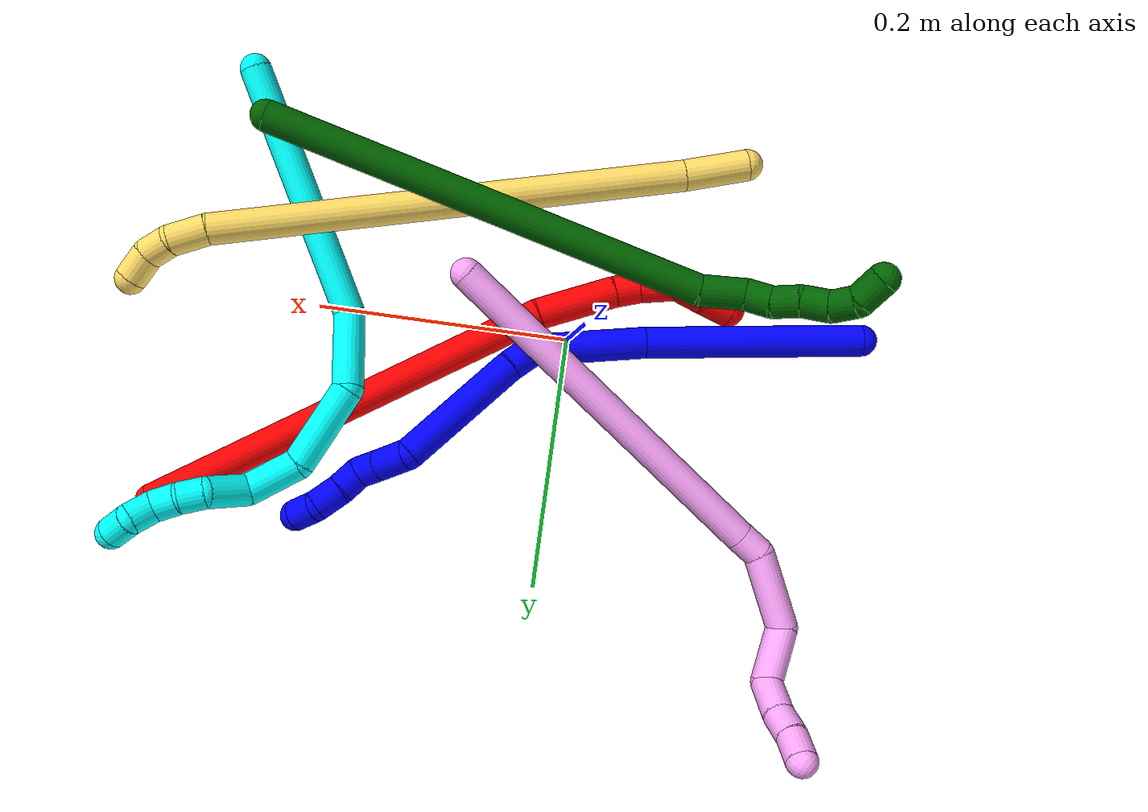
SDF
<sdf version="1.7">
 <world name="default">
  <plugin name="TubeGeneratorPlugin" filename="libtube_generator_plugin.so"/>
  <model name="photoneo_s_sensor">
   <static>1</static>
   <pose>0 0 2 1.57079 1.57079 3.14159</pose>
   <link name="link">
    <inertial><mass>0.1</mass></inertial>
    <sensor name="sensor" type="depth">
     <update_rate>30</update_rate>
     <camera>
      <horizontal_fov>1.22</horizontal_fov>
      <image><width>1920</width><height>1200</height><format>B8G8R8</format></image>
      <clip><near>0.1</near><far>4</far></clip>
      <depth_camera><output>points</output></depth_camera>
     </camera>
     <plugin name="camera_plugin" filename="libgazebo_ros_depth_camera.so">
      <baseline>0.2</baseline>
      <alwaysOn>1</alwaysOn>
      <updateRate>0.0</updateRate>
      <cameraName>camera_ir</cameraName>
      <imageTopicName>/camera/color/image_raw</imageTopicName>
      <cameraInfoTopicName>/camera/color/camera_info</cameraInfoTopicName>
      <depthImageTopicName>/camera/depth/image_raw</depthImageTopicName>
      <depthImageCameraInfoTopicName>/camera/depth/camera_info</depthImageCameraInfoTopicName>
      <pointCloudTopicName>/camera/depth/points</pointCloudTopicName>
      <frameName>fr_optical</frameName>
      <pointCloudCutoff>0.1</pointCloudCutoff>
      <pointCloudCutoffMax>2.0</pointCloudCutoffMax>
      <distortionK1>0</distortionK1>
      <distortionK2>0</distortionK2>
      <distortionK3>0</distortionK3>
      <distortionT1>0</distortionT1>
      <distortionT2>0</distortionT2>
      <CxPrime>0</CxPrime>
      <Cx>0</Cx>
      <Cy>0</Cy>
      <focalLength>0</focalLength>
      <hackBaseline>0</hackBaseline>
     </plugin>
    </sensor>
   </link>
  </model>
  <gravity>0 0 -9.8</gravity>
  <magnetic_field>6e-06 2.3e-05 -4.2e-05</magnetic_field>
  <atmosphere type="adiabatic"/>
  <physics name="default_physics" default="0" type="ode">
   <max_step_size>0.003</max_step_size>
   <real_time_factor>1</real_time_factor>
   <real_time_update_rate>1000</real_time_update_rate>
   <max_contacts>10000</max_contacts>
   <ode>
    <solver>
     <type>quick</type>
     <iters>100</iters>
     <sor>1.3</sor>
     <use_dynamic_moi_rescaling>0</use_dynamic_moi_rescaling>
    </solver>
    <constraints>
     <contact_max_correcting_vel>0</contact_max_correcting_vel>
     <contact_surface_layer>0.001</contact_surface_layer>
     <cfm>0</cfm>
     <erp>0.2</erp>
    </constraints>
   </ode>
  </physics>
  <scene><ambient>0.4 0.4 0.4 1</ambient><background>0.7 0.7 0.7 1</background><shadows>0</shadows></scene>
  <audio><device>default</device></audio>
  <spherical_coordinates>
   <surface_model>EARTH_WGS84</surface_model>
   <latitude_deg>0</latitude_deg>
   <longitude_deg>0</longitude_deg>
   <elevation>0</elevation>
   <heading_deg>0</heading_deg>
  </spherical_coordinates>
  <model name="bin">
   <static>1</static>
   <link name="bottom">
    <collision name="collision-bottom">
     <pose>0 0 -0.01 0 -0 0</pose>
     <geometry><box><size>0.8 0.6 0.02</size></box></geometry>
     <surface>
      <friction><ode><mu>100</mu><mu2>100</mu2></ode></friction>
      <contact><collide_bitmask>65535</collide_bitmask></contact>
     </surface>
    </collision>
   </link>
   <link name="west_wall">
    <collision name="collision-west_wall">
     <pose>-0.41 0 0.1 0 -0 0</pose>
     <geometry><box><size>0.02 0.6 0.2</size></box></geometry>
     <surface>
      <friction><ode><mu>100</mu><mu2>100</mu2></ode></friction>
      <contact><collide_bitmask>65535</collide_bitmask></contact>
     </surface>
    </collision>
   </link>
   <link name="east_wall">
    <collision name="collision-east_wall">
     <pose>0.41 0 0.1 0 -0 0</pose>
     <geometry><box><size>0.02 0.6 0.2</size></box></geometry>
     <surface>
      <friction><ode><mu>100</mu><mu2>100</mu2></ode></friction>
      <contact><collide_bitmask>65535</collide_bitmask></contact>
     </surface>
    </collision>
   </link>
   <link name="south_wall">
    <collision name="collision-south_wall">
     <pose>0 -0.31 0.1 0 -0 0</pose>
     <geometry><box><size>0.8 0.02 0.2</size></box></geometry>
     <surface>
      <friction><ode><mu>100</mu><mu2>100</mu2></ode></friction>
      <contact><collide_bitmask>65535</collide_bitmask></contact>
     </surface>
    </collision>
   </link>
   <link name="north_wall">
    <collision name="collision-north_wall">
     <pose>0 0.31 0.1 0 -0 0</pose>
     <geometry><box><size>0.8 0.02 0.2</size></box></geometry>
     <surface>
      <friction><ode><mu>100</mu><mu2>100</mu2></ode></friction>
      <contact><collide_bitmask>65535</collide_bitmask></contact>
     </surface>
    </collision>
   </link>
  </model>
  <model name="1">
   <static>0</static>
   <link name="1">
    <collision name="collision-cylinder-e_1_1_4">
     <pose>0.058912 0.04021 0.046118 -0.717067 0.766466 -0.299889</pose>
     <geometry><cylinder><radius>0.0125</radius><length>0.169873</length></cylinder></geometry>
     <surface>
      <friction><ode><mu>1.16</mu><mu2>1.16</mu2><slip1>0</slip1><slip2>0</slip2></ode></friction>
      <contact><ode><kp>1e+06</kp><kd>1</kd><max_vel>0</max_vel><min_depth>0.001</min_depth></ode></contact>
     </surface>
    </collision>
    <visual name="visual-cylinder-e_1_1_4">
     <pose>0.058912 0.04021 0.046118 -0.717067 0.766466 -0.299889</pose>
     <geometry><cylinder><radius>0.0125</radius><length>0.169873</length></cylinder></geometry>
     <material><ambient>0 0 1 1</ambient></material>
    </visual>
    <collision name="collision-cylinder-e_2_4_5">
     <pose>0.147063 0.10567 0.114697 -0.843789 0.713265 -0.331381</pose>
     <geometry><cylinder><radius>0.0125</radius><length>0.089377</length></cylinder></geometry>
     <surface>
      <friction><ode><mu>1.16</mu><mu2>1.16</mu2><slip1>0</slip1><slip2>0</slip2></ode></friction>
      <contact><ode><kp>1e+06</kp><kd>1</kd><max_vel>0</max_vel><min_depth>0.001</min_depth></ode></contact>
     </surface>
    </collision>
    <visual name="visual-cylinder-e_2_4_5">
     <pose>0.147063 0.10567 0.114697 -0.843789 0.713265 -0.331381</pose>
     <geometry><cylinder><radius>0.0125</radius><length>0.089377</length></cylinder></geometry>
     <material><ambient>0 0 1 1</ambient></material>
    </visual>
    <collision name="collision-cylinder-e_3_5_6">
     <pose>0.183298 0.139753 0.13734 -1.55015 0.669724 -0.657011</pose>
     <geometry><cylinder><radius>0.0125</radius><length>0.022537</length></cylinder></geometry>
     <surface>
      <friction><ode><mu>1.16</mu><mu2>1.16</mu2><slip1>0</slip1><slip2>0</slip2></ode></friction>
      <contact><ode><kp>1e+06</kp><kd>1</kd><max_vel>0</max_vel><min_depth>0.001</min_depth></ode></contact>
     </surface>
    </collision>
    <visual name="visual-cylinder-e_3_5_6">
     <pose>0.183298 0.139753 0.13734 -1.55015 0.669724 -0.657011</pose>
     <geometry><cylinder><radius>0.0125</radius><length>0.022537</length></cylinder></geometry>
     <material><ambient>0 0 1 1</ambient></material>
    </visual>
    <collision name="collision-cylinder-e_4_6_7">
     <pose>0.223276 0.188843 0.132211 -1.70199 0.682156 -0.769383</pose>
     <geometry><cylinder><radius>0.0125</radius><length>0.104628</length></cylinder></geometry>
     <surface>
      <friction><ode><mu>1.16</mu><mu2>1.16</mu2><slip1>0</slip1><slip2>0</slip2></ode></friction>
      <contact><ode><kp>1e+06</kp><kd>1</kd><max_vel>0</max_vel><min_depth>0.001</min_depth></ode></contact>
     </surface>
    </collision>
    <visual name="visual-cylinder-e_4_6_7">
     <pose>0.223276 0.188843 0.132211 -1.70199 0.682156 -0.769383</pose>
     <geometry><cylinder><radius>0.0125</radius><length>0.104628</length></cylinder></geometry>
     <material><ambient>0 0 1 1</ambient></material>
    </visual>
    <collision name="collision-cylinder-e_5_7_8">
     <pose>0.270756 0.23144 0.128522 -0.964111 1.37692 -0.813016</pose>
     <geometry><cylinder><radius>0.0125</radius><length>0.02955</length></cylinder></geometry>
     <surface>
      <friction><ode><mu>1.16</mu><mu2>1.16</mu2><slip1>0</slip1><slip2>0</slip2></ode></friction>
      <contact><ode><kp>1e+06</kp><kd>1</kd><max_vel>0</max_vel><min_depth>0.001</min_depth></ode></contact>
     </surface>
    </collision>
    <visual name="visual-cylinder-e_5_7_8">
     <pose>0.270756 0.23144 0.128522 -0.964111 1.37692 -0.813016</pose>
     <geometry><cylinder><radius>0.0125</radius><length>0.02955</length></cylinder></geometry>
     <material><ambient>0 0 1 1</ambient></material>
    </visual>
    <collision name="collision-cylinder-e_6_8_9">
     <pose>0.294944 0.236214 0.131722 -0.99593 1.27986 -0.76914</pose>
     <geometry><cylinder><radius>0.0125</radius><length>0.020228</length></cylinder></geometry>
     <surface>
      <friction><ode><mu>1.16</mu><mu2>1.16</mu2><slip1>0</slip1><slip2>0</slip2></ode></friction>
      <contact><ode><kp>1e+06</kp><kd>1</kd><max_vel>0</max_vel><min_depth>0.001</min_depth></ode></contact>
     </surface>
    </collision>
    <visual name="visual-cylinder-e_6_8_9">
     <pose>0.294944 0.236214 0.131722 -0.99593 1.27986 -0.76914</pose>
     <geometry><cylinder><radius>0.0125</radius><length>0.020228</length></cylinder></geometry>
     <material><ambient>0 0 1 1</ambient></material>
    </visual>
    <collision name="collision-cylinder-e_7_9_10">
     <pose>0.310553 0.246689 0.132164 -1.71104 0.629977 -0.717656</pose>
     <geometry><cylinder><radius>0.0125</radius><length>0.020099</length></cylinder></geometry>
     <surface>
      <friction><ode><mu>1.16</mu><mu2>1.16</mu2><slip1>0</slip1><slip2>0</slip2></ode></friction>
      <contact><ode><kp>1e+06</kp><kd>1</kd><max_vel>0</max_vel><min_depth>0.001</min_depth></ode></contact>
     </surface>
    </collision>
    <visual name="visual-cylinder-e_7_9_10">
     <pose>0.310553 0.246689 0.132164 -1.71104 0.629977 -0.717656</pose>
     <geometry><cylinder><radius>0.0125</radius><length>0.020099</length></cylinder></geometry>
     <material><ambient>0 0 1 1</ambient></material>
    </visual>
    <collision name="collision-cylinder-e_8_10_11">
     <pose>0.324403 0.263074 0.131062 -1.56685 0.759912 -0.757195</pose>
     <geometry><cylinder><radius>0.0125</radius><length>0.023022</length></cylinder></geometry>
     <surface>
      <friction><ode><mu>1.16</mu><mu2>1.16</mu2><slip1>0</slip1><slip2>0</slip2></ode></friction>
      <contact><ode><kp>1e+06</kp><kd>1</kd><max_vel>0</max_vel><min_depth>0.001</min_depth></ode></contact>
     </surface>
    </collision>
    <visual name="visual-cylinder-e_8_10_11">
     <pose>0.324403 0.263074 0.131062 -1.56685 0.759912 -0.757195</pose>
     <geometry><cylinder><radius>0.0125</radius><length>0.023022</length></cylinder></geometry>
     <material><ambient>0 0 1 1</ambient></material>
    </visual>
    <collision name="collision-cylinder-e_9_11_2">
     <pose>0.342251 0.274214 0.131978 -1.2651 1.28337 -1.00214</pose>
     <geometry><cylinder><radius>0.0125</radius><length>0.020684</length></cylinder></geometry>
     <surface>
      <friction><ode><mu>1.16</mu><mu2>1.16</mu2><slip1>0</slip1><slip2>0</slip2></ode></friction>
      <contact><ode><kp>1e+06</kp><kd>1</kd><max_vel>0</max_vel><min_depth>0.001</min_depth></ode></contact>
     </surface>
    </collision>
    <visual name="visual-cylinder-e_9_11_2">
     <pose>0.342251 0.274214 0.131978 -1.2651 1.28337 -1.00214</pose>
     <geometry><cylinder><radius>0.0125</radius><length>0.020684</length></cylinder></geometry>
     <material><ambient>0 0 1 1</ambient></material>
    </visual>
    <collision name="collision-sphere-2">
     <pose>0.352169 0.27701 0.13286 0 -0 0</pose>
     <geometry><sphere><radius>0.0125</radius></sphere></geometry>
     <surface>
      <friction><ode><mu>1.16</mu><mu2>1.16</mu2><slip1>0</slip1><slip2>0</slip2></ode></friction>
      <contact><ode><kp>1e+06</kp><kd>1</kd><max_vel>0</max_vel><min_depth>0.001</min_depth></ode></contact>
     </surface>
    </collision>
    <visual name="visual-sphere-2">
     <pose>0.352169 0.27701 0.13286 0 -0 0</pose>
     <geometry><sphere><radius>0.0125</radius></sphere></geometry>
     <material><ambient>0 0 1 1</ambient></material>
    </visual>
    <collision name="collision-sphere-11">
     <pose>0.332333 0.271418 0.131095 0 -0 0</pose>
     <geometry><sphere><radius>0.0125</radius></sphere></geometry>
     <surface>
      <friction><ode><mu>1.16</mu><mu2>1.16</mu2><slip1>0</slip1><slip2>0</slip2></ode></friction>
      <contact><ode><kp>1e+06</kp><kd>1</kd><max_vel>0</max_vel><min_depth>0.001</min_depth></ode></contact>
     </surface>
    </collision>
    <visual name="visual-sphere-11">
     <pose>0.332333 0.271418 0.131095 0 -0 0</pose>
     <geometry><sphere><radius>0.0125</radius></sphere></geometry>
     <material><ambient>0 0 1 1</ambient></material>
    </visual>
    <collision name="collision-sphere-10">
     <pose>0.316474 0.25473 0.131029 0 -0 0</pose>
     <geometry><sphere><radius>0.0125</radius></sphere></geometry>
     <surface>
      <friction><ode><mu>1.16</mu><mu2>1.16</mu2><slip1>0</slip1><slip2>0</slip2></ode></friction>
      <contact><ode><kp>1e+06</kp><kd>1</kd><max_vel>0</max_vel><min_depth>0.001</min_depth></ode></contact>
     </surface>
    </collision>
    <visual name="visual-sphere-10">
     <pose>0.316474 0.25473 0.131029 0 -0 0</pose>
     <geometry><sphere><radius>0.0125</radius></sphere></geometry>
     <material><ambient>0 0 1 1</ambient></material>
    </visual>
    <collision name="collision-sphere-9">
     <pose>0.304633 0.238648 0.133299 0 -0 0</pose>
     <geometry><sphere><radius>0.0125</radius></sphere></geometry>
     <surface>
      <friction><ode><mu>1.16</mu><mu2>1.16</mu2><slip1>0</slip1><slip2>0</slip2></ode></friction>
      <contact><ode><kp>1e+06</kp><kd>1</kd><max_vel>0</max_vel><min_depth>0.001</min_depth></ode></contact>
     </surface>
    </collision>
    <visual name="visual-sphere-9">
     <pose>0.304633 0.238648 0.133299 0 -0 0</pose>
     <geometry><sphere><radius>0.0125</radius></sphere></geometry>
     <material><ambient>0 0 1 1</ambient></material>
    </visual>
    <collision name="collision-sphere-4">
     <pose>0.117823 0.080419 0.092235 0 -0 0</pose>
     <geometry><sphere><radius>0.0125</radius></sphere></geometry>
     <surface>
      <friction><ode><mu>1.16</mu><mu2>1.16</mu2><slip1>0</slip1><slip2>0</slip2></ode></friction>
      <contact><ode><kp>1e+06</kp><kd>1</kd><max_vel>0</max_vel><min_depth>0.001</min_depth></ode></contact>
     </surface>
    </collision>
    <visual name="visual-sphere-4">
     <pose>0.117823 0.080419 0.092235 0 -0 0</pose>
     <geometry><sphere><radius>0.0125</radius></sphere></geometry>
     <material><ambient>0 0 1 1</ambient></material>
    </visual>
    <collision name="collision-sphere-1">
     <geometry><sphere><radius>0.0125</radius></sphere></geometry>
     <surface>
      <friction><ode><mu>1.16</mu><mu2>1.16</mu2><slip1>0</slip1><slip2>0</slip2></ode></friction>
      <contact><ode><kp>1e+06</kp><kd>1</kd><max_vel>0</max_vel><min_depth>0.001</min_depth></ode></contact>
     </surface>
    </collision>
    <visual name="visual-sphere-1">
     <geometry><sphere><radius>0.0125</radius></sphere></geometry>
     <material><ambient>0 0 1 1</ambient></material>
    </visual>
    <collision name="collision-sphere-8">
     <pose>0.285255 0.233779 0.130145 0 -0 0</pose>
     <geometry><sphere><radius>0.0125</radius></sphere></geometry>
     <surface>
      <friction><ode><mu>1.16</mu><mu2>1.16</mu2><slip1>0</slip1><slip2>0</slip2></ode></friction>
      <contact><ode><kp>1e+06</kp><kd>1</kd><max_vel>0</max_vel><min_depth>0.001</min_depth></ode></contact>
     </surface>
    </collision>
    <visual name="visual-sphere-8">
     <pose>0.285255 0.233779 0.130145 0 -0 0</pose>
     <geometry><sphere><radius>0.0125</radius></sphere></geometry>
     <material><ambient>0 0 1 1</ambient></material>
    </visual>
    <collision name="collision-sphere-5">
     <pose>0.176303 0.13092 0.137158 0 -0 0</pose>
     <geometry><sphere><radius>0.0125</radius></sphere></geometry>
     <surface>
      <friction><ode><mu>1.16</mu><mu2>1.16</mu2><slip1>0</slip1><slip2>0</slip2></ode></friction>
      <contact><ode><kp>1e+06</kp><kd>1</kd><max_vel>0</max_vel><min_depth>0.001</min_depth></ode></contact>
     </surface>
    </collision>
    <visual name="visual-sphere-5">
     <pose>0.176303 0.13092 0.137158 0 -0 0</pose>
     <geometry><sphere><radius>0.0125</radius></sphere></geometry>
     <material><ambient>0 0 1 1</ambient></material>
    </visual>
    <collision name="collision-sphere-6">
     <pose>0.190293 0.148585 0.137523 0 -0 0</pose>
     <geometry><sphere><radius>0.0125</radius></sphere></geometry>
     <surface>
      <friction><ode><mu>1.16</mu><mu2>1.16</mu2><slip1>0</slip1><slip2>0</slip2></ode></friction>
      <contact><ode><kp>1e+06</kp><kd>1</kd><max_vel>0</max_vel><min_depth>0.001</min_depth></ode></contact>
     </surface>
    </collision>
    <visual name="visual-sphere-6">
     <pose>0.190293 0.148585 0.137523 0 -0 0</pose>
     <geometry><sphere><radius>0.0125</radius></sphere></geometry>
     <material><ambient>0 0 1 1</ambient></material>
    </visual>
    <collision name="collision-sphere-7">
     <pose>0.256258 0.229101 0.126899 0 -0 0</pose>
     <geometry><sphere><radius>0.0125</radius></sphere></geometry>
     <surface>
      <friction><ode><mu>1.16</mu><mu2>1.16</mu2><slip1>0</slip1><slip2>0</slip2></ode></friction>
      <contact><ode><kp>1e+06</kp><kd>1</kd><max_vel>0</max_vel><min_depth>0.001</min_depth></ode></contact>
     </surface>
    </collision>
    <visual name="visual-sphere-7">
     <pose>0.256258 0.229101 0.126899 0 -0 0</pose>
     <geometry><sphere><radius>0.0125</radius></sphere></geometry>
     <material><ambient>0 0 1 1</ambient></material>
    </visual>
    <inertial>
     <pose>0.1708 0.134974 0.099759 0 -0 0</pose>
     <mass>0.5</mass>
     <inertia>
      <ixx>0.000256</ixx>
      <ixy>0</ixy>
      <ixz>0</ixz>
      <iyy>0.000307</iyy>
      <iyz>0</iyz>
      <izz>-0.000705</izz>
     </inertia>
    </inertial>
   </link>
   <pose>-0.228971 -0.03038 0.015126 1.37428 0.709518 0.600783</pose>
  </model>
  <model name="2">
   <static>0</static>
   <link name="2">
    <collision name="collision-cylinder-e_1_1_4">
     <pose>-0.139965 0.012555 -0.095579 -3.01098 -0.967665 2.89397</pose>
     <geometry><cylinder><radius>0.0125</radius><length>0.339901</length></cylinder></geometry>
     <surface>
      <friction><ode><mu>1.16</mu><mu2>1.16</mu2><slip1>0</slip1><slip2>0</slip2></ode></friction>
      <contact><ode><kp>1e+06</kp><kd>1</kd><max_vel>0</max_vel><min_depth>0.001</min_depth></ode></contact>
     </surface>
    </collision>
    <visual name="visual-cylinder-e_1_1_4">
     <pose>-0.139965 0.012555 -0.095579 -3.01098 -0.967665 2.89397</pose>
     <geometry><cylinder><radius>0.0125</radius><length>0.339901</length></cylinder></geometry>
     <material><ambient>1 0 0 1</ambient></material>
    </visual>
    <collision name="collision-cylinder-e_2_4_5">
     <pose>-0.303663 0.02364 -0.211666 3.07006 -0.856893 -2.98522</pose>
     <geometry><cylinder><radius>0.0125</radius><length>0.062803</length></cylinder></geometry>
     <surface>
      <friction><ode><mu>1.16</mu><mu2>1.16</mu2><slip1>0</slip1><slip2>0</slip2></ode></friction>
      <contact><ode><kp>1e+06</kp><kd>1</kd><max_vel>0</max_vel><min_depth>0.001</min_depth></ode></contact>
     </surface>
    </collision>
    <visual name="visual-cylinder-e_2_4_5">
     <pose>-0.303663 0.02364 -0.211666 3.07006 -0.856893 -2.98522</pose>
     <geometry><cylinder><radius>0.0125</radius><length>0.062803</length></cylinder></geometry>
     <material><ambient>1 0 0 1</ambient></material>
    </visual>
    <collision name="collision-cylinder-e_3_5_6">
     <pose>-0.334648 0.021142 -0.239786 3.00722 -0.756642 -2.80619</pose>
     <geometry><cylinder><radius>0.0125</radius><length>0.021126</length></cylinder></geometry>
     <surface>
      <friction><ode><mu>1.16</mu><mu2>1.16</mu2><slip1>0</slip1><slip2>0</slip2></ode></friction>
      <contact><ode><kp>1e+06</kp><kd>1</kd><max_vel>0</max_vel><min_depth>0.001</min_depth></ode></contact>
     </surface>
    </collision>
    <visual name="visual-cylinder-e_3_5_6">
     <pose>-0.334648 0.021142 -0.239786 3.00722 -0.756642 -2.80619</pose>
     <geometry><cylinder><radius>0.0125</radius><length>0.021126</length></cylinder></geometry>
     <material><ambient>1 0 0 1</ambient></material>
    </visual>
    <collision name="collision-cylinder-e_4_6_7">
     <pose>-0.348607 0.021331 -0.260167 -3.04649 -0.481847 2.75897</pose>
     <geometry><cylinder><radius>0.0125</radius><length>0.02895</length></cylinder></geometry>
     <surface>
      <friction><ode><mu>1.16</mu><mu2>1.16</mu2><slip1>0</slip1><slip2>0</slip2></ode></friction>
      <contact><ode><kp>1e+06</kp><kd>1</kd><max_vel>0</max_vel><min_depth>0.001</min_depth></ode></contact>
     </surface>
    </collision>
    <visual name="visual-cylinder-e_4_6_7">
     <pose>-0.348607 0.021331 -0.260167 -3.04649 -0.481847 2.75897</pose>
     <geometry><cylinder><radius>0.0125</radius><length>0.02895</length></cylinder></geometry>
     <material><ambient>1 0 0 1</ambient></material>
    </visual>
    <collision name="collision-cylinder-e_5_7_8">
     <pose>-0.357573 0.01686 -0.283011 2.62758 -0.192745 -0.704941</pose>
     <geometry><cylinder><radius>0.0125</radius><length>0.023578</length></cylinder></geometry>
     <surface>
      <friction><ode><mu>1.16</mu><mu2>1.16</mu2><slip1>0</slip1><slip2>0</slip2></ode></friction>
      <contact><ode><kp>1e+06</kp><kd>1</kd><max_vel>0</max_vel><min_depth>0.001</min_depth></ode></contact>
     </surface>
    </collision>
    <visual name="visual-cylinder-e_5_7_8">
     <pose>-0.357573 0.01686 -0.283011 2.62758 -0.192745 -0.704941</pose>
     <geometry><cylinder><radius>0.0125</radius><length>0.023578</length></cylinder></geometry>
     <material><ambient>1 0 0 1</ambient></material>
    </visual>
    <collision name="collision-cylinder-e_6_8_2">
     <pose>-0.363283 0.004103 -0.301912 2.46633 -0.296292 -0.803907</pose>
     <geometry><cylinder><radius>0.0125</radius><length>0.023644</length></cylinder></geometry>
     <surface>
      <friction><ode><mu>1.16</mu><mu2>1.16</mu2><slip1>0</slip1><slip2>0</slip2></ode></friction>
      <contact><ode><kp>1e+06</kp><kd>1</kd><max_vel>0</max_vel><min_depth>0.001</min_depth></ode></contact>
     </surface>
    </collision>
    <visual name="visual-cylinder-e_6_8_2">
     <pose>-0.363283 0.004103 -0.301912 2.46633 -0.296292 -0.803907</pose>
     <geometry><cylinder><radius>0.0125</radius><length>0.023644</length></cylinder></geometry>
     <material><ambient>1 0 0 1</ambient></material>
    </visual>
    <collision name="collision-sphere-2">
     <pose>-0.366735 -0.002965 -0.310737 0 -0 0</pose>
     <geometry><sphere><radius>0.0125</radius></sphere></geometry>
     <surface>
      <friction><ode><mu>1.16</mu><mu2>1.16</mu2><slip1>0</slip1><slip2>0</slip2></ode></friction>
      <contact><ode><kp>1e+06</kp><kd>1</kd><max_vel>0</max_vel><min_depth>0.001</min_depth></ode></contact>
     </surface>
    </collision>
    <visual name="visual-sphere-2">
     <pose>-0.366735 -0.002965 -0.310737 0 -0 0</pose>
     <geometry><sphere><radius>0.0125</radius></sphere></geometry>
     <material><ambient>1 0 0 1</ambient></material>
    </visual>
    <collision name="collision-sphere-4">
     <pose>-0.27993 0.02511 -0.191158 0 -0 0</pose>
     <geometry><sphere><radius>0.0125</radius></sphere></geometry>
     <surface>
      <friction><ode><mu>1.16</mu><mu2>1.16</mu2><slip1>0</slip1><slip2>0</slip2></ode></friction>
      <contact><ode><kp>1e+06</kp><kd>1</kd><max_vel>0</max_vel><min_depth>0.001</min_depth></ode></contact>
     </surface>
    </collision>
    <visual name="visual-sphere-4">
     <pose>-0.27993 0.02511 -0.191158 0 -0 0</pose>
     <geometry><sphere><radius>0.0125</radius></sphere></geometry>
     <material><ambient>1 0 0 1</ambient></material>
    </visual>
    <collision name="collision-sphere-1">
     <geometry><sphere><radius>0.0125</radius></sphere></geometry>
     <surface>
      <friction><ode><mu>1.16</mu><mu2>1.16</mu2><slip1>0</slip1><slip2>0</slip2></ode></friction>
      <contact><ode><kp>1e+06</kp><kd>1</kd><max_vel>0</max_vel><min_depth>0.001</min_depth></ode></contact>
     </surface>
    </collision>
    <visual name="visual-sphere-1">
     <geometry><sphere><radius>0.0125</radius></sphere></geometry>
     <material><ambient>1 0 0 1</ambient></material>
    </visual>
    <collision name="collision-sphere-8">
     <pose>-0.359831 0.011171 -0.293086 0 -0 0</pose>
     <geometry><sphere><radius>0.0125</radius></sphere></geometry>
     <surface>
      <friction><ode><mu>1.16</mu><mu2>1.16</mu2><slip1>0</slip1><slip2>0</slip2></ode></friction>
      <contact><ode><kp>1e+06</kp><kd>1</kd><max_vel>0</max_vel><min_depth>0.001</min_depth></ode></contact>
     </surface>
    </collision>
    <visual name="visual-sphere-8">
     <pose>-0.359831 0.011171 -0.293086 0 -0 0</pose>
     <geometry><sphere><radius>0.0125</radius></sphere></geometry>
     <material><ambient>1 0 0 1</ambient></material>
    </visual>
    <collision name="collision-sphere-5">
     <pose>-0.327397 0.022171 -0.232175 0 -0 0</pose>
     <geometry><sphere><radius>0.0125</radius></sphere></geometry>
     <surface>
      <friction><ode><mu>1.16</mu><mu2>1.16</mu2><slip1>0</slip1><slip2>0</slip2></ode></friction>
      <contact><ode><kp>1e+06</kp><kd>1</kd><max_vel>0</max_vel><min_depth>0.001</min_depth></ode></contact>
     </surface>
    </collision>
    <visual name="visual-sphere-5">
     <pose>-0.327397 0.022171 -0.232175 0 -0 0</pose>
     <geometry><sphere><radius>0.0125</radius></sphere></geometry>
     <material><ambient>1 0 0 1</ambient></material>
    </visual>
    <collision name="collision-sphere-6">
     <pose>-0.341899 0.020113 -0.247398 0 -0 0</pose>
     <geometry><sphere><radius>0.0125</radius></sphere></geometry>
     <surface>
      <friction><ode><mu>1.16</mu><mu2>1.16</mu2><slip1>0</slip1><slip2>0</slip2></ode></friction>
      <contact><ode><kp>1e+06</kp><kd>1</kd><max_vel>0</max_vel><min_depth>0.001</min_depth></ode></contact>
     </surface>
    </collision>
    <visual name="visual-sphere-6">
     <pose>-0.341899 0.020113 -0.247398 0 -0 0</pose>
     <geometry><sphere><radius>0.0125</radius></sphere></geometry>
     <material><ambient>1 0 0 1</ambient></material>
    </visual>
    <collision name="collision-sphere-7">
     <pose>-0.355315 0.022549 -0.272936 0 -0 0</pose>
     <geometry><sphere><radius>0.0125</radius></sphere></geometry>
     <surface>
      <friction><ode><mu>1.16</mu><mu2>1.16</mu2><slip1>0</slip1><slip2>0</slip2></ode></friction>
      <contact><ode><kp>1e+06</kp><kd>1</kd><max_vel>0</max_vel><min_depth>0.001</min_depth></ode></contact>
     </surface>
    </collision>
    <visual name="visual-sphere-7">
     <pose>-0.355315 0.022549 -0.272936 0 -0 0</pose>
     <geometry><sphere><radius>0.0125</radius></sphere></geometry>
     <material><ambient>1 0 0 1</ambient></material>
    </visual>
    <inertial>
     <pose>-0.201654 0.014621 -0.144378 0 -0 0</pose>
     <mass>0.5</mass>
     <inertia>
      <ixx>-0.001399</ixx>
      <ixy>0</ixy>
      <ixz>0</ixz>
      <iyy>0.003722</iyy>
      <iyz>0</iyz>
      <izz>0.002463</izz>
     </inertia>
    </inertial>
   </link>
   <pose>0.309583 0.170618 0.0115 2.0459 -0.362821 1.06852</pose>
  </model>
  <model name="3">
   <static>0</static>
   <link name="3">
    <collision name="collision-cylinder-e_1_1_4">
     <pose>0.016314 0.098937 -0.026025 -1.82802 0.158133 -0.204818</pose>
     <geometry><cylinder><radius>0.0125</radius><length>0.20719</length></cylinder></geometry>
     <surface>
      <friction><ode><mu>1.16</mu><mu2>1.16</mu2><slip1>0</slip1><slip2>0</slip2></ode></friction>
      <contact><ode><kp>1e+06</kp><kd>1</kd><max_vel>0</max_vel><min_depth>0.001</min_depth></ode></contact>
     </surface>
    </collision>
    <visual name="visual-cylinder-e_1_1_4">
     <pose>0.016314 0.098937 -0.026025 -1.82802 0.158133 -0.204818</pose>
     <geometry><cylinder><radius>0.0125</radius><length>0.20719</length></cylinder></geometry>
     <material><ambient>0.003922 1 0.996078 1</ambient></material>
    </visual>
    <collision name="collision-cylinder-e_2_4_5">
     <pose>0.021778 0.22656 -0.063094 -1.93828 -0.339312 0.489026</pose>
     <geometry><cylinder><radius>0.0125</radius><length>0.065194</length></cylinder></geometry>
     <surface>
      <friction><ode><mu>1.16</mu><mu2>1.16</mu2><slip1>0</slip1><slip2>0</slip2></ode></friction>
      <contact><ode><kp>1e+06</kp><kd>1</kd><max_vel>0</max_vel><min_depth>0.001</min_depth></ode></contact>
     </surface>
    </collision>
    <visual name="visual-cylinder-e_2_4_5">
     <pose>0.021778 0.22656 -0.063094 -1.93828 -0.339312 0.489026</pose>
     <geometry><cylinder><radius>0.0125</radius><length>0.065194</length></cylinder></geometry>
     <material><ambient>0.003922 1 0.996078 1</ambient></material>
    </visual>
    <collision name="collision-cylinder-e_3_5_6">
     <pose>-0.008244 0.281788 -0.064609 -1.22616 -0.597076 0.426411</pose>
     <geometry><cylinder><radius>0.0125</radius><length>0.068202</length></cylinder></geometry>
     <surface>
      <friction><ode><mu>1.16</mu><mu2>1.16</mu2><slip1>0</slip1><slip2>0</slip2></ode></friction>
      <contact><ode><kp>1e+06</kp><kd>1</kd><max_vel>0</max_vel><min_depth>0.001</min_depth></ode></contact>
     </surface>
    </collision>
    <visual name="visual-cylinder-e_3_5_6">
     <pose>-0.008244 0.281788 -0.064609 -1.22616 -0.597076 0.426411</pose>
     <geometry><cylinder><radius>0.0125</radius><length>0.068202</length></cylinder></geometry>
     <material><ambient>0.003922 1 0.996078 1</ambient></material>
    </visual>
    <collision name="collision-cylinder-e_4_6_7">
     <pose>-0.043726 0.31682 -0.042912 -0.609097 -0.832596 0.276184</pose>
     <geometry><cylinder><radius>0.0125</radius><length>0.044098</length></cylinder></geometry>
     <surface>
      <friction><ode><mu>1.16</mu><mu2>1.16</mu2><slip1>0</slip1><slip2>0</slip2></ode></friction>
      <contact><ode><kp>1e+06</kp><kd>1</kd><max_vel>0</max_vel><min_depth>0.001</min_depth></ode></contact>
     </surface>
    </collision>
    <visual name="visual-cylinder-e_4_6_7">
     <pose>-0.043726 0.31682 -0.042912 -0.609097 -0.832596 0.276184</pose>
     <geometry><cylinder><radius>0.0125</radius><length>0.044098</length></cylinder></geometry>
     <material><ambient>0.003922 1 0.996078 1</ambient></material>
    </visual>
    <collision name="collision-cylinder-e_5_7_8">
     <pose>-0.077155 0.323424 -0.030021 1.20542 -1.45346 -1.09806</pose>
     <geometry><cylinder><radius>0.0125</radius><length>0.034477</length></cylinder></geometry>
     <surface>
      <friction><ode><mu>1.16</mu><mu2>1.16</mu2><slip1>0</slip1><slip2>0</slip2></ode></friction>
      <contact><ode><kp>1e+06</kp><kd>1</kd><max_vel>0</max_vel><min_depth>0.001</min_depth></ode></contact>
     </surface>
    </collision>
    <visual name="visual-cylinder-e_5_7_8">
     <pose>-0.077155 0.323424 -0.030021 1.20542 -1.45346 -1.09806</pose>
     <geometry><cylinder><radius>0.0125</radius><length>0.034477</length></cylinder></geometry>
     <material><ambient>0.003922 1 0.996078 1</ambient></material>
    </visual>
    <collision name="collision-cylinder-e_6_8_9">
     <pose>-0.103013 0.322666 -0.024137 -0.214713 -1.02688 0.121391</pose>
     <geometry><cylinder><radius>0.0125</radius><length>0.020424</length></cylinder></geometry>
     <surface>
      <friction><ode><mu>1.16</mu><mu2>1.16</mu2><slip1>0</slip1><slip2>0</slip2></ode></friction>
      <contact><ode><kp>1e+06</kp><kd>1</kd><max_vel>0</max_vel><min_depth>0.001</min_depth></ode></contact>
     </surface>
    </collision>
    <visual name="visual-cylinder-e_6_8_9">
     <pose>-0.103013 0.322666 -0.024137 -0.214713 -1.02688 0.121391</pose>
     <geometry><cylinder><radius>0.0125</radius><length>0.020424</length></cylinder></geometry>
     <material><ambient>0.003922 1 0.996078 1</ambient></material>
    </visual>
    <collision name="collision-cylinder-e_7_9_10">
     <pose>-0.118953 0.326115 -0.012167 -0.328924 -0.786021 0.137391</pose>
     <geometry><cylinder><radius>0.0125</radius><length>0.020357</length></cylinder></geometry>
     <surface>
      <friction><ode><mu>1.16</mu><mu2>1.16</mu2><slip1>0</slip1><slip2>0</slip2></ode></friction>
      <contact><ode><kp>1e+06</kp><kd>1</kd><max_vel>0</max_vel><min_depth>0.001</min_depth></ode></contact>
     </surface>
    </collision>
    <visual name="visual-cylinder-e_7_9_10">
     <pose>-0.118953 0.326115 -0.012167 -0.328924 -0.786021 0.137391</pose>
     <geometry><cylinder><radius>0.0125</radius><length>0.020357</length></cylinder></geometry>
     <material><ambient>0.003922 1 0.996078 1</ambient></material>
    </visual>
    <collision name="collision-cylinder-e_8_10_11">
     <pose>-0.135287 0.331978 -0.003295 -1.04292 -1.14904 0.71212</pose>
     <geometry><cylinder><radius>0.0125</radius><length>0.020018</length></cylinder></geometry>
     <surface>
      <friction><ode><mu>1.16</mu><mu2>1.16</mu2><slip1>0</slip1><slip2>0</slip2></ode></friction>
      <contact><ode><kp>1e+06</kp><kd>1</kd><max_vel>0</max_vel><min_depth>0.001</min_depth></ode></contact>
     </surface>
    </collision>
    <visual name="visual-cylinder-e_8_10_11">
     <pose>-0.135287 0.331978 -0.003295 -1.04292 -1.14904 0.71212</pose>
     <geometry><cylinder><radius>0.0125</radius><length>0.020018</length></cylinder></geometry>
     <material><ambient>0.003922 1 0.996078 1</ambient></material>
    </visual>
    <collision name="collision-cylinder-e_9_11_2">
     <pose>-0.149073 0.340578 0.006058 -0.60679 -0.483068 0.153936</pose>
     <geometry><cylinder><radius>0.0125</radius><length>0.020041</length></cylinder></geometry>
     <surface>
      <friction><ode><mu>1.16</mu><mu2>1.16</mu2><slip1>0</slip1><slip2>0</slip2></ode></friction>
      <contact><ode><kp>1e+06</kp><kd>1</kd><max_vel>0</max_vel><min_depth>0.001</min_depth></ode></contact>
     </surface>
    </collision>
    <visual name="visual-cylinder-e_9_11_2">
     <pose>-0.149073 0.340578 0.006058 -0.60679 -0.483068 0.153936</pose>
     <geometry><cylinder><radius>0.0125</radius><length>0.020041</length></cylinder></geometry>
     <material><ambient>0.003922 1 0.996078 1</ambient></material>
    </visual>
    <collision name="collision-sphere-2">
     <pose>-0.153728 0.345638 0.013348 0 -0 0</pose>
     <geometry><sphere><radius>0.0125</radius></sphere></geometry>
     <surface>
      <friction><ode><mu>1.16</mu><mu2>1.16</mu2><slip1>0</slip1><slip2>0</slip2></ode></friction>
      <contact><ode><kp>1e+06</kp><kd>1</kd><max_vel>0</max_vel><min_depth>0.001</min_depth></ode></contact>
     </surface>
    </collision>
    <visual name="visual-sphere-2">
     <pose>-0.153728 0.345638 0.013348 0 -0 0</pose>
     <geometry><sphere><radius>0.0125</radius></sphere></geometry>
     <material><ambient>0.003922 1 0.996078 1</ambient></material>
    </visual>
    <collision name="collision-sphere-11">
     <pose>-0.144419 0.335518 -0.001232 0 -0 0</pose>
     <geometry><sphere><radius>0.0125</radius></sphere></geometry>
     <surface>
      <friction><ode><mu>1.16</mu><mu2>1.16</mu2><slip1>0</slip1><slip2>0</slip2></ode></friction>
      <contact><ode><kp>1e+06</kp><kd>1</kd><max_vel>0</max_vel><min_depth>0.001</min_depth></ode></contact>
     </surface>
    </collision>
    <visual name="visual-sphere-11">
     <pose>-0.144419 0.335518 -0.001232 0 -0 0</pose>
     <geometry><sphere><radius>0.0125</radius></sphere></geometry>
     <material><ambient>0.003922 1 0.996078 1</ambient></material>
    </visual>
    <collision name="collision-sphere-10">
     <pose>-0.126155 0.328438 -0.005359 0 -0 0</pose>
     <geometry><sphere><radius>0.0125</radius></sphere></geometry>
     <surface>
      <friction><ode><mu>1.16</mu><mu2>1.16</mu2><slip1>0</slip1><slip2>0</slip2></ode></friction>
      <contact><ode><kp>1e+06</kp><kd>1</kd><max_vel>0</max_vel><min_depth>0.001</min_depth></ode></contact>
     </surface>
    </collision>
    <visual name="visual-sphere-10">
     <pose>-0.126155 0.328438 -0.005359 0 -0 0</pose>
     <geometry><sphere><radius>0.0125</radius></sphere></geometry>
     <material><ambient>0.003922 1 0.996078 1</ambient></material>
    </visual>
    <collision name="collision-sphere-9">
     <pose>-0.111751 0.323792 -0.018974 0 -0 0</pose>
     <geometry><sphere><radius>0.0125</radius></sphere></geometry>
     <surface>
      <friction><ode><mu>1.16</mu><mu2>1.16</mu2><slip1>0</slip1><slip2>0</slip2></ode></friction>
      <contact><ode><kp>1e+06</kp><kd>1</kd><max_vel>0</max_vel><min_depth>0.001</min_depth></ode></contact>
     </surface>
    </collision>
    <visual name="visual-sphere-9">
     <pose>-0.111751 0.323792 -0.018974 0 -0 0</pose>
     <geometry><sphere><radius>0.0125</radius></sphere></geometry>
     <material><ambient>0.003922 1 0.996078 1</ambient></material>
    </visual>
    <collision name="collision-sphere-4">
     <pose>0.032627 0.197873 -0.05205 0 -0 0</pose>
     <geometry><sphere><radius>0.0125</radius></sphere></geometry>
     <surface>
      <friction><ode><mu>1.16</mu><mu2>1.16</mu2><slip1>0</slip1><slip2>0</slip2></ode></friction>
      <contact><ode><kp>1e+06</kp><kd>1</kd><max_vel>0</max_vel><min_depth>0.001</min_depth></ode></contact>
     </surface>
    </collision>
    <visual name="visual-sphere-4">
     <pose>0.032627 0.197873 -0.05205 0 -0 0</pose>
     <geometry><sphere><radius>0.0125</radius></sphere></geometry>
     <material><ambient>0.003922 1 0.996078 1</ambient></material>
    </visual>
    <collision name="collision-sphere-1">
     <geometry><sphere><radius>0.0125</radius></sphere></geometry>
     <surface>
      <friction><ode><mu>1.16</mu><mu2>1.16</mu2><slip1>0</slip1><slip2>0</slip2></ode></friction>
      <contact><ode><kp>1e+06</kp><kd>1</kd><max_vel>0</max_vel><min_depth>0.001</min_depth></ode></contact>
     </surface>
    </collision>
    <visual name="visual-sphere-1">
     <geometry><sphere><radius>0.0125</radius></sphere></geometry>
     <material><ambient>0.003922 1 0.996078 1</ambient></material>
    </visual>
    <collision name="collision-sphere-8">
     <pose>-0.094275 0.32154 -0.0293 0 -0 0</pose>
     <geometry><sphere><radius>0.0125</radius></sphere></geometry>
     <surface>
      <friction><ode><mu>1.16</mu><mu2>1.16</mu2><slip1>0</slip1><slip2>0</slip2></ode></friction>
      <contact><ode><kp>1e+06</kp><kd>1</kd><max_vel>0</max_vel><min_depth>0.001</min_depth></ode></contact>
     </surface>
    </collision>
    <visual name="visual-sphere-8">
     <pose>-0.094275 0.32154 -0.0293 0 -0 0</pose>
     <geometry><sphere><radius>0.0125</radius></sphere></geometry>
     <material><ambient>0.003922 1 0.996078 1</ambient></material>
    </visual>
    <collision name="collision-sphere-5">
     <pose>0.010928 0.255246 -0.074137 0 -0 0</pose>
     <geometry><sphere><radius>0.0125</radius></sphere></geometry>
     <surface>
      <friction><ode><mu>1.16</mu><mu2>1.16</mu2><slip1>0</slip1><slip2>0</slip2></ode></friction>
      <contact><ode><kp>1e+06</kp><kd>1</kd><max_vel>0</max_vel><min_depth>0.001</min_depth></ode></contact>
     </surface>
    </collision>
    <visual name="visual-sphere-5">
     <pose>0.010928 0.255246 -0.074137 0 -0 0</pose>
     <geometry><sphere><radius>0.0125</radius></sphere></geometry>
     <material><ambient>0.003922 1 0.996078 1</ambient></material>
    </visual>
    <collision name="collision-sphere-6">
     <pose>-0.027417 0.308331 -0.055081 0 -0 0</pose>
     <geometry><sphere><radius>0.0125</radius></sphere></geometry>
     <surface>
      <friction><ode><mu>1.16</mu><mu2>1.16</mu2><slip1>0</slip1><slip2>0</slip2></ode></friction>
      <contact><ode><kp>1e+06</kp><kd>1</kd><max_vel>0</max_vel><min_depth>0.001</min_depth></ode></contact>
     </surface>
    </collision>
    <visual name="visual-sphere-6">
     <pose>-0.027417 0.308331 -0.055081 0 -0 0</pose>
     <geometry><sphere><radius>0.0125</radius></sphere></geometry>
     <material><ambient>0.003922 1 0.996078 1</ambient></material>
    </visual>
    <collision name="collision-sphere-7">
     <pose>-0.060035 0.325309 -0.030742 0 -0 0</pose>
     <geometry><sphere><radius>0.0125</radius></sphere></geometry>
     <surface>
      <friction><ode><mu>1.16</mu><mu2>1.16</mu2><slip1>0</slip1><slip2>0</slip2></ode></friction>
      <contact><ode><kp>1e+06</kp><kd>1</kd><max_vel>0</max_vel><min_depth>0.001</min_depth></ode></contact>
     </surface>
    </collision>
    <visual name="visual-sphere-7">
     <pose>-0.060035 0.325309 -0.030742 0 -0 0</pose>
     <geometry><sphere><radius>0.0125</radius></sphere></geometry>
     <material><ambient>0.003922 1 0.996078 1</ambient></material>
    </visual>
    <inertial>
     <pose>-0.021144 0.212618 -0.035049 0 -0 0</pose>
     <mass>0.5</mass>
     <inertia>
      <ixx>0.000638</ixx>
      <ixy>0</ixy>
      <ixz>0</ixz>
      <iyy>-0.000234</iyy>
      <iyz>0</iyz>
      <izz>-0.000842</izz>
     </inertia>
    </inertial>
   </link>
   <pose>0.274023 -0.178251 0.012158 -3.00633 0.656345 -2.83799</pose>
  </model>
  <model name="4">
   <static>0</static>
   <link name="4">
    <collision name="collision-cylinder-e_1_1_4">
     <pose>-0.082282 0.023158 0.1216 -0.18819 -0.586653 0.056994</pose>
     <geometry><cylinder><radius>0.0125</radius><length>0.297276</length></cylinder></geometry>
     <surface>
      <friction><ode><mu>1.16</mu><mu2>1.16</mu2><slip1>0</slip1><slip2>0</slip2></ode></friction>
      <contact><ode><kp>1e+06</kp><kd>1</kd><max_vel>0</max_vel><min_depth>0.001</min_depth></ode></contact>
     </surface>
    </collision>
    <visual name="visual-cylinder-e_1_1_4">
     <pose>-0.082282 0.023158 0.1216 -0.18819 -0.586653 0.056994</pose>
     <geometry><cylinder><radius>0.0125</radius><length>0.297276</length></cylinder></geometry>
     <material><ambient>1 0.65098 0.996078 1</ambient></material>
    </visual>
    <collision name="collision-cylinder-e_2_4_5">
     <pose>-0.169957 0.047648 0.252334 -0.14478 -0.528655 0.03925</pose>
     <geometry><cylinder><radius>0.0125</radius><length>0.021381</length></cylinder></geometry>
     <surface>
      <friction><ode><mu>1.16</mu><mu2>1.16</mu2><slip1>0</slip1><slip2>0</slip2></ode></friction>
      <contact><ode><kp>1e+06</kp><kd>1</kd><max_vel>0</max_vel><min_depth>0.001</min_depth></ode></contact>
     </surface>
    </collision>
    <visual name="visual-cylinder-e_2_4_5">
     <pose>-0.169957 0.047648 0.252334 -0.14478 -0.528655 0.03925</pose>
     <geometry><cylinder><radius>0.0125</radius><length>0.021381</length></cylinder></geometry>
     <material><ambient>1 0.65098 0.996078 1</ambient></material>
    </visual>
    <collision name="collision-cylinder-e_3_5_6">
     <pose>-0.186835 0.067805 0.283217 -0.713485 -0.379922 0.143076</pose>
     <geometry><cylinder><radius>0.0125</radius><length>0.061945</length></cylinder></geometry>
     <surface>
      <friction><ode><mu>1.16</mu><mu2>1.16</mu2><slip1>0</slip1><slip2>0</slip2></ode></friction>
      <contact><ode><kp>1e+06</kp><kd>1</kd><max_vel>0</max_vel><min_depth>0.001</min_depth></ode></contact>
     </surface>
    </collision>
    <visual name="visual-cylinder-e_3_5_6">
     <pose>-0.186835 0.067805 0.283217 -0.713485 -0.379922 0.143076</pose>
     <geometry><cylinder><radius>0.0125</radius><length>0.061945</length></cylinder></geometry>
     <material><ambient>1 0.65098 0.996078 1</ambient></material>
    </visual>
    <collision name="collision-cylinder-e_4_6_7">
     <pose>-0.194959 0.107241 0.313324 -1.1855 0.150008 -0.101141</pose>
     <geometry><cylinder><radius>0.0125</radius><length>0.044989</length></cylinder></geometry>
     <surface>
      <friction><ode><mu>1.16</mu><mu2>1.16</mu2><slip1>0</slip1><slip2>0</slip2></ode></friction>
      <contact><ode><kp>1e+06</kp><kd>1</kd><max_vel>0</max_vel><min_depth>0.001</min_depth></ode></contact>
     </surface>
    </collision>
    <visual name="visual-cylinder-e_4_6_7">
     <pose>-0.194959 0.107241 0.313324 -1.1855 0.150008 -0.101141</pose>
     <geometry><cylinder><radius>0.0125</radius><length>0.044989</length></cylinder></geometry>
     <material><ambient>1 0.65098 0.996078 1</ambient></material>
    </visual>
    <collision name="collision-cylinder-e_5_7_8">
     <pose>-0.184557 0.133787 0.33371 -0.458395 0.483479 -0.114917</pose>
     <geometry><cylinder><radius>0.0125</radius><length>0.030293</length></cylinder></geometry>
     <surface>
      <friction><ode><mu>1.16</mu><mu2>1.16</mu2><slip1>0</slip1><slip2>0</slip2></ode></friction>
      <contact><ode><kp>1e+06</kp><kd>1</kd><max_vel>0</max_vel><min_depth>0.001</min_depth></ode></contact>
     </surface>
    </collision>
    <visual name="visual-cylinder-e_5_7_8">
     <pose>-0.184557 0.133787 0.33371 -0.458395 0.483479 -0.114917</pose>
     <geometry><cylinder><radius>0.0125</radius><length>0.030293</length></cylinder></geometry>
     <material><ambient>1 0.65098 0.996078 1</ambient></material>
    </visual>
    <collision name="collision-cylinder-e_6_8_9">
     <pose>-0.172282 0.142041 0.354887 -0.248309 0.50616 -0.064529</pose>
     <geometry><cylinder><radius>0.0125</radius><length>0.02159</length></cylinder></geometry>
     <surface>
      <friction><ode><mu>1.16</mu><mu2>1.16</mu2><slip1>0</slip1><slip2>0</slip2></ode></friction>
      <contact><ode><kp>1e+06</kp><kd>1</kd><max_vel>0</max_vel><min_depth>0.001</min_depth></ode></contact>
     </surface>
    </collision>
    <visual name="visual-cylinder-e_6_8_9">
     <pose>-0.172282 0.142041 0.354887 -0.248309 0.50616 -0.064529</pose>
     <geometry><cylinder><radius>0.0125</radius><length>0.02159</length></cylinder></geometry>
     <material><ambient>1 0.65098 0.996078 1</ambient></material>
    </visual>
    <collision name="collision-cylinder-e_7_9_2">
     <pose>-0.161416 0.14854 0.372852 -0.442747 0.5237 -0.120489</pose>
     <geometry><cylinder><radius>0.0125</radius><length>0.022527</length></cylinder></geometry>
     <surface>
      <friction><ode><mu>1.16</mu><mu2>1.16</mu2><slip1>0</slip1><slip2>0</slip2></ode></friction>
      <contact><ode><kp>1e+06</kp><kd>1</kd><max_vel>0</max_vel><min_depth>0.001</min_depth></ode></contact>
     </surface>
    </collision>
    <visual name="visual-cylinder-e_7_9_2">
     <pose>-0.161416 0.14854 0.372852 -0.442747 0.5237 -0.120489</pose>
     <geometry><cylinder><radius>0.0125</radius><length>0.022527</length></cylinder></geometry>
     <material><ambient>1 0.65098 0.996078 1</ambient></material>
    </visual>
    <collision name="collision-sphere-2">
     <pose>-0.155783 0.152719 0.381665 0 -0 0</pose>
     <geometry><sphere><radius>0.0125</radius></sphere></geometry>
     <surface>
      <friction><ode><mu>1.16</mu><mu2>1.16</mu2><slip1>0</slip1><slip2>0</slip2></ode></friction>
      <contact><ode><kp>1e+06</kp><kd>1</kd><max_vel>0</max_vel><min_depth>0.001</min_depth></ode></contact>
     </surface>
    </collision>
    <visual name="visual-sphere-2">
     <pose>-0.155783 0.152719 0.381665 0 -0 0</pose>
     <geometry><sphere><radius>0.0125</radius></sphere></geometry>
     <material><ambient>1 0.65098 0.996078 1</ambient></material>
    </visual>
    <collision name="collision-sphere-9">
     <pose>-0.167049 0.144361 0.364039 0 -0 0</pose>
     <geometry><sphere><radius>0.0125</radius></sphere></geometry>
     <surface>
      <friction><ode><mu>1.16</mu><mu2>1.16</mu2><slip1>0</slip1><slip2>0</slip2></ode></friction>
      <contact><ode><kp>1e+06</kp><kd>1</kd><max_vel>0</max_vel><min_depth>0.001</min_depth></ode></contact>
     </surface>
    </collision>
    <visual name="visual-sphere-9">
     <pose>-0.167049 0.144361 0.364039 0 -0 0</pose>
     <geometry><sphere><radius>0.0125</radius></sphere></geometry>
     <material><ambient>1 0.65098 0.996078 1</ambient></material>
    </visual>
    <collision name="collision-sphere-4">
     <pose>-0.164565 0.046316 0.2432 0 -0 0</pose>
     <geometry><sphere><radius>0.0125</radius></sphere></geometry>
     <surface>
      <friction><ode><mu>1.16</mu><mu2>1.16</mu2><slip1>0</slip1><slip2>0</slip2></ode></friction>
      <contact><ode><kp>1e+06</kp><kd>1</kd><max_vel>0</max_vel><min_depth>0.001</min_depth></ode></contact>
     </surface>
    </collision>
    <visual name="visual-sphere-4">
     <pose>-0.164565 0.046316 0.2432 0 -0 0</pose>
     <geometry><sphere><radius>0.0125</radius></sphere></geometry>
     <material><ambient>1 0.65098 0.996078 1</ambient></material>
    </visual>
    <collision name="collision-sphere-1">
     <geometry><sphere><radius>0.0125</radius></sphere></geometry>
     <surface>
      <friction><ode><mu>1.16</mu><mu2>1.16</mu2><slip1>0</slip1><slip2>0</slip2></ode></friction>
      <contact><ode><kp>1e+06</kp><kd>1</kd><max_vel>0</max_vel><min_depth>0.001</min_depth></ode></contact>
     </surface>
    </collision>
    <visual name="visual-sphere-1">
     <geometry><sphere><radius>0.0125</radius></sphere></geometry>
     <material><ambient>1 0.65098 0.996078 1</ambient></material>
    </visual>
    <collision name="collision-sphere-8">
     <pose>-0.177516 0.139721 0.345735 0 -0 0</pose>
     <geometry><sphere><radius>0.0125</radius></sphere></geometry>
     <surface>
      <friction><ode><mu>1.16</mu><mu2>1.16</mu2><slip1>0</slip1><slip2>0</slip2></ode></friction>
      <contact><ode><kp>1e+06</kp><kd>1</kd><max_vel>0</max_vel><min_depth>0.001</min_depth></ode></contact>
     </surface>
    </collision>
    <visual name="visual-sphere-8">
     <pose>-0.177516 0.139721 0.345735 0 -0 0</pose>
     <geometry><sphere><radius>0.0125</radius></sphere></geometry>
     <material><ambient>1 0.65098 0.996078 1</ambient></material>
    </visual>
    <collision name="collision-sphere-5">
     <pose>-0.175349 0.04898 0.261469 0 -0 0</pose>
     <geometry><sphere><radius>0.0125</radius></sphere></geometry>
     <surface>
      <friction><ode><mu>1.16</mu><mu2>1.16</mu2><slip1>0</slip1><slip2>0</slip2></ode></friction>
      <contact><ode><kp>1e+06</kp><kd>1</kd><max_vel>0</max_vel><min_depth>0.001</min_depth></ode></contact>
     </surface>
    </collision>
    <visual name="visual-sphere-5">
     <pose>-0.175349 0.04898 0.261469 0 -0 0</pose>
     <geometry><sphere><radius>0.0125</radius></sphere></geometry>
     <material><ambient>1 0.65098 0.996078 1</ambient></material>
    </visual>
    <collision name="collision-sphere-6">
     <pose>-0.198321 0.08663 0.304965 0 -0 0</pose>
     <geometry><sphere><radius>0.0125</radius></sphere></geometry>
     <surface>
      <friction><ode><mu>1.16</mu><mu2>1.16</mu2><slip1>0</slip1><slip2>0</slip2></ode></friction>
      <contact><ode><kp>1e+06</kp><kd>1</kd><max_vel>0</max_vel><min_depth>0.001</min_depth></ode></contact>
     </surface>
    </collision>
    <visual name="visual-sphere-6">
     <pose>-0.198321 0.08663 0.304965 0 -0 0</pose>
     <geometry><sphere><radius>0.0125</radius></sphere></geometry>
     <material><ambient>1 0.65098 0.996078 1</ambient></material>
    </visual>
    <collision name="collision-sphere-7">
     <pose>-0.191598 0.127852 0.321684 0 -0 0</pose>
     <geometry><sphere><radius>0.0125</radius></sphere></geometry>
     <surface>
      <friction><ode><mu>1.16</mu><mu2>1.16</mu2><slip1>0</slip1><slip2>0</slip2></ode></friction>
      <contact><ode><kp>1e+06</kp><kd>1</kd><max_vel>0</max_vel><min_depth>0.001</min_depth></ode></contact>
     </surface>
    </collision>
    <visual name="visual-sphere-7">
     <pose>-0.191598 0.127852 0.321684 0 -0 0</pose>
     <geometry><sphere><radius>0.0125</radius></sphere></geometry>
     <material><ambient>1 0.65098 0.996078 1</ambient></material>
    </visual>
    <inertial>
     <pose>-0.122771 0.054787 0.198708 0 -0 0</pose>
     <mass>0.5</mass>
     <inertia>
      <ixx>0.001961</ixx>
      <ixy>0</ixy>
      <ixz>0</ixz>
      <iyy>0.002318</iyy>
      <iyz>0</iyz>
      <izz>0.000885</izz>
     </inertia>
    </inertial>
   </link>
   <pose>0.085124 -0.036457 0.051565 -0.158514 -1.08182 -0.332227</pose>
  </model>
  <model name="5">
   <static>0</static>
   <link name="5">
    <collision name="collision-cylinder-e_1_1_4">
     <pose>0.00969 -0.001319 0.023381 0.056374 0.392328 0.011205</pose>
     <geometry><cylinder><radius>0.0125</radius><length>0.050688</length></cylinder></geometry>
     <surface>
      <friction><ode><mu>1.16</mu><mu2>1.16</mu2><slip1>0</slip1><slip2>0</slip2></ode></friction>
      <contact><ode><kp>1e+06</kp><kd>1</kd><max_vel>0</max_vel><min_depth>0.001</min_depth></ode></contact>
     </surface>
    </collision>
    <visual name="visual-cylinder-e_1_1_4">
     <pose>0.00969 -0.001319 0.023381 0.056374 0.392328 0.011205</pose>
     <geometry><cylinder><radius>0.0125</radius><length>0.050688</length></cylinder></geometry>
     <material><ambient>1 0.858824 0.4 1</ambient></material>
    </visual>
    <collision name="collision-cylinder-e_2_4_5">
     <pose>0.077891 -0.010335 0.224134 0.043364 0.318356 0.006963</pose>
     <geometry><cylinder><radius>0.0125</radius><length>0.373863</length></cylinder></geometry>
     <surface>
      <friction><ode><mu>1.16</mu><mu2>1.16</mu2><slip1>0</slip1><slip2>0</slip2></ode></friction>
      <contact><ode><kp>1e+06</kp><kd>1</kd><max_vel>0</max_vel><min_depth>0.001</min_depth></ode></contact>
     </surface>
    </collision>
    <visual name="visual-cylinder-e_2_4_5">
     <pose>0.077891 -0.010335 0.224134 0.043364 0.318356 0.006963</pose>
     <geometry><cylinder><radius>0.0125</radius><length>0.373863</length></cylinder></geometry>
     <material><ambient>1 0.858824 0.4 1</ambient></material>
    </visual>
    <collision name="collision-cylinder-e_3_5_6">
     <pose>0.143495 -0.017492 0.414952 -0.040082 0.485144 -0.009919</pose>
     <geometry><cylinder><radius>0.0125</radius><length>0.030425</length></cylinder></geometry>
     <surface>
      <friction><ode><mu>1.16</mu><mu2>1.16</mu2><slip1>0</slip1><slip2>0</slip2></ode></friction>
      <contact><ode><kp>1e+06</kp><kd>1</kd><max_vel>0</max_vel><min_depth>0.001</min_depth></ode></contact>
     </surface>
    </collision>
    <visual name="visual-cylinder-e_3_5_6">
     <pose>0.143495 -0.017492 0.414952 -0.040082 0.485144 -0.009919</pose>
     <geometry><cylinder><radius>0.0125</radius><length>0.030425</length></cylinder></geometry>
     <material><ambient>1 0.858824 0.4 1</ambient></material>
    </visual>
    <collision name="collision-cylinder-e_4_6_7">
     <pose>0.158413 -0.017104 0.435801 0.020405 0.812852 0.008782</pose>
     <geometry><cylinder><radius>0.0125</radius><length>0.021544</length></cylinder></geometry>
     <surface>
      <friction><ode><mu>1.16</mu><mu2>1.16</mu2><slip1>0</slip1><slip2>0</slip2></ode></friction>
      <contact><ode><kp>1e+06</kp><kd>1</kd><max_vel>0</max_vel><min_depth>0.001</min_depth></ode></contact>
     </surface>
    </collision>
    <visual name="visual-cylinder-e_4_6_7">
     <pose>0.158413 -0.017104 0.435801 0.020405 0.812852 0.008782</pose>
     <geometry><cylinder><radius>0.0125</radius><length>0.021544</length></cylinder></geometry>
     <material><ambient>1 0.858824 0.4 1</ambient></material>
    </visual>
    <collision name="collision-cylinder-e_5_7_2">
     <pose>0.175655 -0.012996 0.44877 -0.653256 0.931133 -0.337158</pose>
     <geometry><cylinder><radius>0.0125</radius><length>0.02348</length></cylinder></geometry>
     <surface>
      <friction><ode><mu>1.16</mu><mu2>1.16</mu2><slip1>0</slip1><slip2>0</slip2></ode></friction>
      <contact><ode><kp>1e+06</kp><kd>1</kd><max_vel>0</max_vel><min_depth>0.001</min_depth></ode></contact>
     </surface>
    </collision>
    <visual name="visual-cylinder-e_5_7_2">
     <pose>0.175655 -0.012996 0.44877 -0.653256 0.931133 -0.337158</pose>
     <geometry><cylinder><radius>0.0125</radius><length>0.02348</length></cylinder></geometry>
     <material><ambient>1 0.858824 0.4 1</ambient></material>
    </visual>
    <collision name="collision-sphere-2">
     <pose>0.185074 -0.008737 0.454335 0 -0 0</pose>
     <geometry><sphere><radius>0.0125</radius></sphere></geometry>
     <surface>
      <friction><ode><mu>1.16</mu><mu2>1.16</mu2><slip1>0</slip1><slip2>0</slip2></ode></friction>
      <contact><ode><kp>1e+06</kp><kd>1</kd><max_vel>0</max_vel><min_depth>0.001</min_depth></ode></contact>
     </surface>
    </collision>
    <visual name="visual-sphere-2">
     <pose>0.185074 -0.008737 0.454335 0 -0 0</pose>
     <geometry><sphere><radius>0.0125</radius></sphere></geometry>
     <material><ambient>1 0.858824 0.4 1</ambient></material>
    </visual>
    <collision name="collision-sphere-7">
     <pose>0.166236 -0.017255 0.443205 0 -0 0</pose>
     <geometry><sphere><radius>0.0125</radius></sphere></geometry>
     <surface>
      <friction><ode><mu>1.16</mu><mu2>1.16</mu2><slip1>0</slip1><slip2>0</slip2></ode></friction>
      <contact><ode><kp>1e+06</kp><kd>1</kd><max_vel>0</max_vel><min_depth>0.001</min_depth></ode></contact>
     </surface>
    </collision>
    <visual name="visual-sphere-7">
     <pose>0.166236 -0.017255 0.443205 0 -0 0</pose>
     <geometry><sphere><radius>0.0125</radius></sphere></geometry>
     <material><ambient>1 0.858824 0.4 1</ambient></material>
    </visual>
    <collision name="collision-sphere-6">
     <pose>0.15059 -0.016953 0.428398 0 -0 0</pose>
     <geometry><sphere><radius>0.0125</radius></sphere></geometry>
     <surface>
      <friction><ode><mu>1.16</mu><mu2>1.16</mu2><slip1>0</slip1><slip2>0</slip2></ode></friction>
      <contact><ode><kp>1e+06</kp><kd>1</kd><max_vel>0</max_vel><min_depth>0.001</min_depth></ode></contact>
     </surface>
    </collision>
    <visual name="visual-sphere-6">
     <pose>0.15059 -0.016953 0.428398 0 -0 0</pose>
     <geometry><sphere><radius>0.0125</radius></sphere></geometry>
     <material><ambient>1 0.858824 0.4 1</ambient></material>
    </visual>
    <collision name="collision-sphere-5">
     <pose>0.136401 -0.018032 0.401505 0 -0 0</pose>
     <geometry><sphere><radius>0.0125</radius></sphere></geometry>
     <surface>
      <friction><ode><mu>1.16</mu><mu2>1.16</mu2><slip1>0</slip1><slip2>0</slip2></ode></friction>
      <contact><ode><kp>1e+06</kp><kd>1</kd><max_vel>0</max_vel><min_depth>0.001</min_depth></ode></contact>
     </surface>
    </collision>
    <visual name="visual-sphere-5">
     <pose>0.136401 -0.018032 0.401505 0 -0 0</pose>
     <geometry><sphere><radius>0.0125</radius></sphere></geometry>
     <material><ambient>1 0.858824 0.4 1</ambient></material>
    </visual>
    <collision name="collision-sphere-1">
     <geometry><sphere><radius>0.0125</radius></sphere></geometry>
     <surface>
      <friction><ode><mu>1.16</mu><mu2>1.16</mu2><slip1>0</slip1><slip2>0</slip2></ode></friction>
      <contact><ode><kp>1e+06</kp><kd>1</kd><max_vel>0</max_vel><min_depth>0.001</min_depth></ode></contact>
     </surface>
    </collision>
    <visual name="visual-sphere-1">
     <geometry><sphere><radius>0.0125</radius></sphere></geometry>
     <material><ambient>1 0.858824 0.4 1</ambient></material>
    </visual>
    <collision name="collision-sphere-4">
     <pose>0.01938 -0.002639 0.046762 0 -0 0</pose>
     <geometry><sphere><radius>0.0125</radius></sphere></geometry>
     <surface>
      <friction><ode><mu>1.16</mu><mu2>1.16</mu2><slip1>0</slip1><slip2>0</slip2></ode></friction>
      <contact><ode><kp>1e+06</kp><kd>1</kd><max_vel>0</max_vel><min_depth>0.001</min_depth></ode></contact>
     </surface>
    </collision>
    <visual name="visual-sphere-4">
     <pose>0.01938 -0.002639 0.046762 0 -0 0</pose>
     <geometry><sphere><radius>0.0125</radius></sphere></geometry>
     <material><ambient>1 0.858824 0.4 1</ambient></material>
    </visual>
    <inertial>
     <pose>0.083029 -0.010273 0.235063 0 -0 0</pose>
     <mass>0.5</mass>
     <inertia>
      <ixx>0.00421</ixx>
      <ixy>0</ixy>
      <ixz>0</ixz>
      <iyy>0.004413</iyy>
      <iyz>0</iyz>
      <izz>-0.001162</izz>
     </inertia>
    </inertial>
   </link>
   <pose>-0.121486 -0.156105 0.012339 1.11429 0.725283 1.32238</pose>
  </model>
  <model name="6">
   <static>0</static>
   <link name="6">
    <collision name="collision-cylinder-e_1_1_4">
     <pose>0.001748 0.002344 -0.177163 -3.12836 0.009866 -1.28148</pose>
     <geometry><cylinder><radius>0.0125</radius><length>0.354374</length></cylinder></geometry>
     <surface>
      <friction><ode><mu>1.16</mu><mu2>1.16</mu2><slip1>0</slip1><slip2>0</slip2></ode></friction>
      <contact><ode><kp>1e+06</kp><kd>1</kd><max_vel>0</max_vel><min_depth>0.001</min_depth></ode></contact>
     </surface>
    </collision>
    <visual name="visual-cylinder-e_1_1_4">
     <pose>0.001748 0.002344 -0.177163 -3.12836 0.009866 -1.28148</pose>
     <geometry><cylinder><radius>0.0125</radius><length>0.354374</length></cylinder></geometry>
     <material><ambient>0 0.392157 0.003922 1</ambient></material>
    </visual>
    <collision name="collision-cylinder-e_2_4_5">
     <pose>0.004906 0.010014 -0.371443 -2.83995 0.078464 -0.505515</pose>
     <geometry><cylinder><radius>0.0125</radius><length>0.035965</length></cylinder></geometry>
     <surface>
      <friction><ode><mu>1.16</mu><mu2>1.16</mu2><slip1>0</slip1><slip2>0</slip2></ode></friction>
      <contact><ode><kp>1e+06</kp><kd>1</kd><max_vel>0</max_vel><min_depth>0.001</min_depth></ode></contact>
     </surface>
    </collision>
    <visual name="visual-cylinder-e_2_4_5">
     <pose>0.004906 0.010014 -0.371443 -2.83995 0.078464 -0.505515</pose>
     <geometry><cylinder><radius>0.0125</radius><length>0.035965</length></cylinder></geometry>
     <material><ambient>0 0.392157 0.003922 1</ambient></material>
    </visual>
    <collision name="collision-cylinder-e_3_5_6">
     <pose>0.010806 0.015847 -0.398156 -3.08885 0.437152 -2.90519</pose>
     <geometry><cylinder><radius>0.0125</radius><length>0.021212</length></cylinder></geometry>
     <surface>
      <friction><ode><mu>1.16</mu><mu2>1.16</mu2><slip1>0</slip1><slip2>0</slip2></ode></friction>
      <contact><ode><kp>1e+06</kp><kd>1</kd><max_vel>0</max_vel><min_depth>0.001</min_depth></ode></contact>
     </surface>
    </collision>
    <visual name="visual-cylinder-e_3_5_6">
     <pose>0.010806 0.015847 -0.398156 -3.08885 0.437152 -2.90519</pose>
     <geometry><cylinder><radius>0.0125</radius><length>0.021212</length></cylinder></geometry>
     <material><ambient>0 0.392157 0.003922 1</ambient></material>
    </visual>
    <collision name="collision-cylinder-e_4_6_7">
     <pose>0.020091 0.020237 -0.416641 -2.72968 0.459028 -1.68237</pose>
     <geometry><cylinder><radius>0.0125</radius><length>0.021643</length></cylinder></geometry>
     <surface>
      <friction><ode><mu>1.16</mu><mu2>1.16</mu2><slip1>0</slip1><slip2>0</slip2></ode></friction>
      <contact><ode><kp>1e+06</kp><kd>1</kd><max_vel>0</max_vel><min_depth>0.001</min_depth></ode></contact>
     </surface>
    </collision>
    <visual name="visual-cylinder-e_4_6_7">
     <pose>0.020091 0.020237 -0.416641 -2.72968 0.459028 -1.68237</pose>
     <geometry><cylinder><radius>0.0125</radius><length>0.021643</length></cylinder></geometry>
     <material><ambient>0 0.392157 0.003922 1</ambient></material>
    </visual>
    <collision name="collision-cylinder-e_5_7_8">
     <pose>0.028962 0.025886 -0.435746 -2.97051 0.37471 -2.29202</pose>
     <geometry><cylinder><radius>0.0125</radius><length>0.022278</length></cylinder></geometry>
     <surface>
      <friction><ode><mu>1.16</mu><mu2>1.16</mu2><slip1>0</slip1><slip2>0</slip2></ode></friction>
      <contact><ode><kp>1e+06</kp><kd>1</kd><max_vel>0</max_vel><min_depth>0.001</min_depth></ode></contact>
     </surface>
    </collision>
    <visual name="visual-cylinder-e_5_7_8">
     <pose>0.028962 0.025886 -0.435746 -2.97051 0.37471 -2.29202</pose>
     <geometry><cylinder><radius>0.0125</radius><length>0.022278</length></cylinder></geometry>
     <material><ambient>0 0.392157 0.003922 1</ambient></material>
    </visual>
    <collision name="collision-cylinder-e_6_8_9">
     <pose>0.039706 0.032267 -0.452726 -2.54286 0.683205 -1.71178</pose>
     <geometry><cylinder><radius>0.0125</radius><length>0.021121</length></cylinder></geometry>
     <surface>
      <friction><ode><mu>1.16</mu><mu2>1.16</mu2><slip1>0</slip1><slip2>0</slip2></ode></friction>
      <contact><ode><kp>1e+06</kp><kd>1</kd><max_vel>0</max_vel><min_depth>0.001</min_depth></ode></contact>
     </surface>
    </collision>
    <visual name="visual-cylinder-e_6_8_9">
     <pose>0.039706 0.032267 -0.452726 -2.54286 0.683205 -1.71178</pose>
     <geometry><cylinder><radius>0.0125</radius><length>0.021121</length></cylinder></geometry>
     <material><ambient>0 0.392157 0.003922 1</ambient></material>
    </visual>
    <collision name="collision-cylinder-e_7_9_2">
     <pose>0.050865 0.046947 -0.463431 -1.94384 0.393924 -0.568913</pose>
     <geometry><cylinder><radius>0.0125</radius><length>0.023407</length></cylinder></geometry>
     <surface>
      <friction><ode><mu>1.16</mu><mu2>1.16</mu2><slip1>0</slip1><slip2>0</slip2></ode></friction>
      <contact><ode><kp>1e+06</kp><kd>1</kd><max_vel>0</max_vel><min_depth>0.001</min_depth></ode></contact>
     </surface>
    </collision>
    <visual name="visual-cylinder-e_7_9_2">
     <pose>0.050865 0.046947 -0.463431 -1.94384 0.393924 -0.568913</pose>
     <geometry><cylinder><radius>0.0125</radius><length>0.023407</length></cylinder></geometry>
     <material><ambient>0 0.392157 0.003922 1</ambient></material>
    </visual>
    <collision name="collision-sphere-2">
     <pose>0.055357 0.057011 -0.467369 0 -0 0</pose>
     <geometry><sphere><radius>0.0125</radius></sphere></geometry>
     <surface>
      <friction><ode><mu>1.16</mu><mu2>1.16</mu2><slip1>0</slip1><slip2>0</slip2></ode></friction>
      <contact><ode><kp>1e+06</kp><kd>1</kd><max_vel>0</max_vel><min_depth>0.001</min_depth></ode></contact>
     </surface>
    </collision>
    <visual name="visual-sphere-2">
     <pose>0.055357 0.057011 -0.467369 0 -0 0</pose>
     <geometry><sphere><radius>0.0125</radius></sphere></geometry>
     <material><ambient>0 0.392157 0.003922 1</ambient></material>
    </visual>
    <collision name="collision-sphere-9">
     <pose>0.046373 0.036883 -0.459492 0 -0 0</pose>
     <geometry><sphere><radius>0.0125</radius></sphere></geometry>
     <surface>
      <friction><ode><mu>1.16</mu><mu2>1.16</mu2><slip1>0</slip1><slip2>0</slip2></ode></friction>
      <contact><ode><kp>1e+06</kp><kd>1</kd><max_vel>0</max_vel><min_depth>0.001</min_depth></ode></contact>
     </surface>
    </collision>
    <visual name="visual-sphere-9">
     <pose>0.046373 0.036883 -0.459492 0 -0 0</pose>
     <geometry><sphere><radius>0.0125</radius></sphere></geometry>
     <material><ambient>0 0.392157 0.003922 1</ambient></material>
    </visual>
    <collision name="collision-sphere-4">
     <pose>0.003496 0.004688 -0.354325 0 -0 0</pose>
     <geometry><sphere><radius>0.0125</radius></sphere></geometry>
     <surface>
      <friction><ode><mu>1.16</mu><mu2>1.16</mu2><slip1>0</slip1><slip2>0</slip2></ode></friction>
      <contact><ode><kp>1e+06</kp><kd>1</kd><max_vel>0</max_vel><min_depth>0.001</min_depth></ode></contact>
     </surface>
    </collision>
    <visual name="visual-sphere-4">
     <pose>0.003496 0.004688 -0.354325 0 -0 0</pose>
     <geometry><sphere><radius>0.0125</radius></sphere></geometry>
     <material><ambient>0 0.392157 0.003922 1</ambient></material>
    </visual>
    <collision name="collision-sphere-1">
     <geometry><sphere><radius>0.0125</radius></sphere></geometry>
     <surface>
      <friction><ode><mu>1.16</mu><mu2>1.16</mu2><slip1>0</slip1><slip2>0</slip2></ode></friction>
      <contact><ode><kp>1e+06</kp><kd>1</kd><max_vel>0</max_vel><min_depth>0.001</min_depth></ode></contact>
     </surface>
    </collision>
    <visual name="visual-sphere-1">
     <geometry><sphere><radius>0.0125</radius></sphere></geometry>
     <material><ambient>0 0.392157 0.003922 1</ambient></material>
    </visual>
    <collision name="collision-sphere-8">
     <pose>0.033039 0.027651 -0.445961 0 -0 0</pose>
     <geometry><sphere><radius>0.0125</radius></sphere></geometry>
     <surface>
      <friction><ode><mu>1.16</mu><mu2>1.16</mu2><slip1>0</slip1><slip2>0</slip2></ode></friction>
      <contact><ode><kp>1e+06</kp><kd>1</kd><max_vel>0</max_vel><min_depth>0.001</min_depth></ode></contact>
     </surface>
    </collision>
    <visual name="visual-sphere-8">
     <pose>0.033039 0.027651 -0.445961 0 -0 0</pose>
     <geometry><sphere><radius>0.0125</radius></sphere></geometry>
     <material><ambient>0 0.392157 0.003922 1</ambient></material>
    </visual>
    <collision name="collision-sphere-5">
     <pose>0.006315 0.01534 -0.388561 0 -0 0</pose>
     <geometry><sphere><radius>0.0125</radius></sphere></geometry>
     <surface>
      <friction><ode><mu>1.16</mu><mu2>1.16</mu2><slip1>0</slip1><slip2>0</slip2></ode></friction>
      <contact><ode><kp>1e+06</kp><kd>1</kd><max_vel>0</max_vel><min_depth>0.001</min_depth></ode></contact>
     </surface>
    </collision>
    <visual name="visual-sphere-5">
     <pose>0.006315 0.01534 -0.388561 0 -0 0</pose>
     <geometry><sphere><radius>0.0125</radius></sphere></geometry>
     <material><ambient>0 0.392157 0.003922 1</ambient></material>
    </visual>
    <collision name="collision-sphere-6">
     <pose>0.015296 0.016353 -0.407751 0 -0 0</pose>
     <geometry><sphere><radius>0.0125</radius></sphere></geometry>
     <surface>
      <friction><ode><mu>1.16</mu><mu2>1.16</mu2><slip1>0</slip1><slip2>0</slip2></ode></friction>
      <contact><ode><kp>1e+06</kp><kd>1</kd><max_vel>0</max_vel><min_depth>0.001</min_depth></ode></contact>
     </surface>
    </collision>
    <visual name="visual-sphere-6">
     <pose>0.015296 0.016353 -0.407751 0 -0 0</pose>
     <geometry><sphere><radius>0.0125</radius></sphere></geometry>
     <material><ambient>0 0.392157 0.003922 1</ambient></material>
    </visual>
    <collision name="collision-sphere-7">
     <pose>0.024885 0.024121 -0.425531 0 -0 0</pose>
     <geometry><sphere><radius>0.0125</radius></sphere></geometry>
     <surface>
      <friction><ode><mu>1.16</mu><mu2>1.16</mu2><slip1>0</slip1><slip2>0</slip2></ode></friction>
      <contact><ode><kp>1e+06</kp><kd>1</kd><max_vel>0</max_vel><min_depth>0.001</min_depth></ode></contact>
     </surface>
    </collision>
    <visual name="visual-sphere-7">
     <pose>0.024885 0.024121 -0.425531 0 -0 0</pose>
     <geometry><sphere><radius>0.0125</radius></sphere></geometry>
     <material><ambient>0 0.392157 0.003922 1</ambient></material>
    </visual>
    <inertial>
     <pose>0.008269 0.008644 -0.247442 0 -0 0</pose>
     <mass>0.5</mass>
     <inertia>
      <ixx>-0.002506</ixx>
      <ixy>0</ixy>
      <ixz>0</ixz>
      <iyy>-0.004633</iyy>
      <iyz>0</iyz>
      <izz>-0.000132</izz>
     </inertia>
    </inertial>
   </link>
   <pose>0.251408 -0.1341 0.055458 0.324566 -1.53032 2.56093</pose>
  </model>
 </world>
</sdf>
